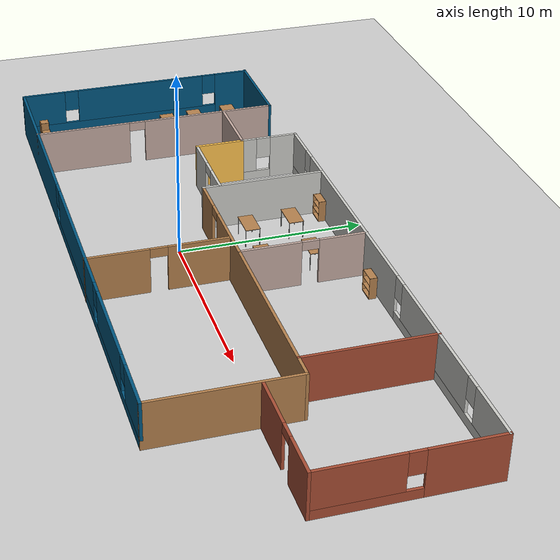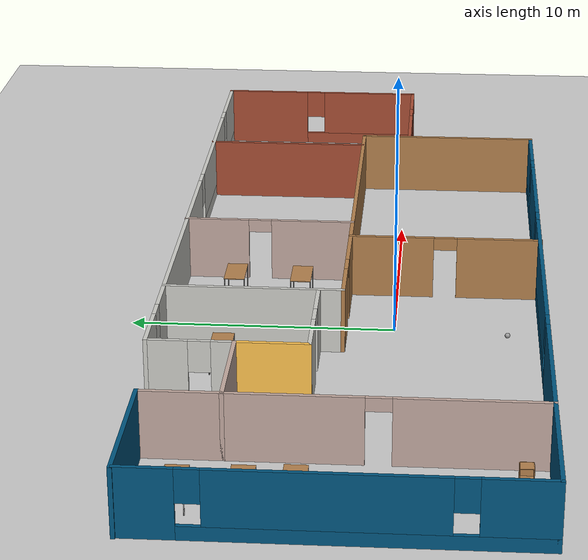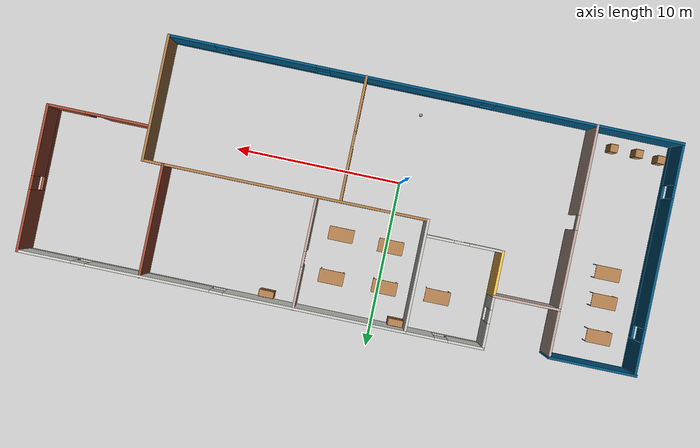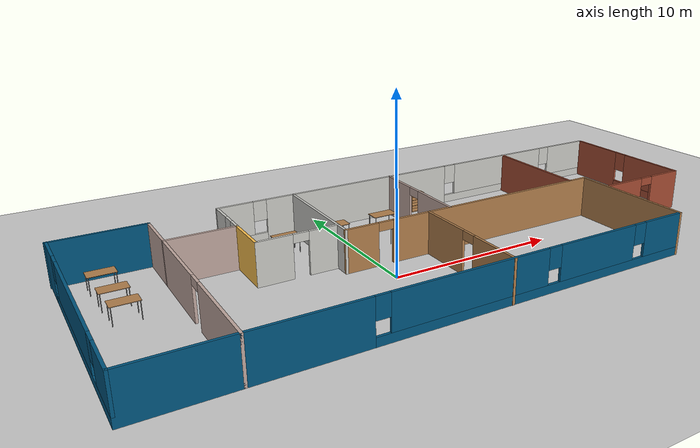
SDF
<sdf version="1.7">
 <world name="default">
  <light name="sun" type="directional">
   <pose>0 0 10 0 -0 0</pose>
   <diffuse>0.8 0.8 0.8 1</diffuse>
   <specular>0.2 0.2 0.2 1</specular>
   <attenuation>
    <range>1000</range>
    <constant>0.9</constant>
    <linear>0.01</linear>
    <quadratic>0.001</quadratic>
   </attenuation>
   <direction>-0.5 0.1 -0.9</direction>
   <spot><inner_angle>0</inner_angle><outer_angle>0</outer_angle><falloff>0</falloff></spot>
  </light>
  <model name="ground_plane">
   <static>1</static>
   <link name="link">
    <collision name="collision">
     <geometry><plane><normal>0 0 1</normal><size>100 100</size></plane></geometry>
     <surface>
      <contact><collide_bitmask>65535</collide_bitmask></contact>
      <friction><ode><mu>100</mu><mu2>50</mu2></ode></friction>
     </surface>
    </collision>
    <visual name="visual">
     <cast_shadows>0</cast_shadows>
     <geometry><plane><normal>0 0 1</normal><size>100 100</size></plane></geometry>
     <material>
      <script><uri>file://media/materials/scripts/gazebo.material</uri><name>Gazebo/Grey</name></script>
     </material>
    </visual>
   </link>
  </model>
  <gravity>0 0 -9.8</gravity>
  <magnetic_field>6e-06 2.3e-05 -4.2e-05</magnetic_field>
  <atmosphere type="adiabatic"/>
  <physics type="ode">
   <max_step_size>0.001</max_step_size>
   <real_time_factor>1</real_time_factor>
   <real_time_update_rate>1000</real_time_update_rate>
  </physics>
  <scene><ambient>0.4 0.4 0.4 1</ambient><background>0.7 0.7 0.7 1</background><shadows>1</shadows></scene>
  <spherical_coordinates>
   <surface_model>EARTH_WGS84</surface_model>
   <latitude_deg>0</latitude_deg>
   <longitude_deg>0</longitude_deg>
   <elevation>0</elevation>
   <heading_deg>0</heading_deg>
  </spherical_coordinates>
  <model name="sohini_building">
   <pose>2.69266 1.47265 0 0 -0 0</pose>
   <link name="Wall_10">
    <collision name="Wall_10_Collision">
     <geometry><box><size>4 0.15 2.5</size></box></geometry>
     <pose>0 0 1.25 0 -0 0</pose>
    </collision>
    <visual name="Wall_10_Visual">
     <pose>0 0 1.25 0 -0 0</pose>
     <geometry><box><size>4 0.15 2.5</size></box></geometry>
     <material>
      <script><uri>file://media/materials/scripts/gazebo.material</uri><name>Gazebo/Grey</name></script>
      <ambient>0.760784 0.662745 0.627451 1</ambient>
     </material>
     <meta><layer>0</layer></meta>
    </visual>
    <pose>-11.175 3.87696 0 0 -0 3.14159</pose>
   </link>
   <link name="Wall_11">
    <collision name="Wall_11_Collision">
     <geometry><box><size>2.93882 0.15 2.5</size></box></geometry>
     <pose>0 0 1.25 0 -0 0</pose>
    </collision>
    <visual name="Wall_11_Visual">
     <pose>0 0 1.25 0 -0 0</pose>
     <geometry><box><size>2.93882 0.15 2.5</size></box></geometry>
     <material>
      <script><uri>file://media/materials/scripts/gazebo.material</uri><name>Gazebo/Grey</name></script>
      <ambient>0.760784 0.662745 0.627451 1</ambient>
     </material>
     <meta><layer>0</layer></meta>
    </visual>
    <pose>-13.1 5.27137 0 0 -0 1.5708</pose>
   </link>
   <link name="Wall_12">
    <collision name="Wall_12_Collision">
     <geometry><box><size>5.25 0.15 2.5</size></box></geometry>
     <pose>0 0 1.25 0 -0 0</pose>
    </collision>
    <visual name="Wall_12_Visual">
     <pose>0 0 1.25 0 -0 0</pose>
     <geometry><box><size>5.25 0.15 2.5</size></box></geometry>
     <material>
      <script><uri>file://media/materials/scripts/gazebo.material</uri><name>Gazebo/Grey</name></script>
      <ambient>0 0.333333 0.498039 1</ambient>
     </material>
     <meta><layer>0</layer></meta>
    </visual>
    <pose>-15.65 6.69637 0 0 -0 3.14159</pose>
   </link>
   <link name="Wall_14">
    <pose>6.775 6.97696 0 0 -0 0</pose>
    <visual name="Wall_14_Visual_0">
     <pose>-6.08464 0 1.25 0 -0 0</pose>
     <geometry><box><size>10.8307 0.15 2.5</size></box></geometry>
     <material>
      <script><uri>file://media/materials/scripts/gazebo.material</uri><name>Gazebo/CeilingTiled</name></script>
      <ambient>0.435294 0.796078 0.67451 1</ambient>
     </material>
     <meta><layer>0</layer></meta>
    </visual>
    <collision name="Wall_14_Collision_0">
     <geometry><box><size>10.8307 0.15 2.5</size></box></geometry>
     <pose>-6.08464 0 1.25 0 -0 0</pose>
    </collision>
    <visual name="Wall_14_Visual_1">
     <pose>5.41536 0 0.25 0 -0 0</pose>
     <geometry><box><size>12.1693 0.15 0.5</size></box></geometry>
     <material>
      <script><uri>file://media/materials/scripts/gazebo.material</uri><name>Gazebo/CeilingTiled</name></script>
      <ambient>0.435294 0.796078 0.67451 1</ambient>
     </material>
     <meta><layer>0</layer></meta>
    </visual>
    <collision name="Wall_14_Collision_1">
     <geometry><box><size>12.1693 0.15 0.5</size></box></geometry>
     <pose>5.41536 0 0.25 0 -0 0</pose>
    </collision>
    <visual name="Wall_14_Visual_2">
     <pose>3.79922 0 1.5 0 -0 0</pose>
     <geometry><box><size>7.337 0.15 2</size></box></geometry>
     <material>
      <script><uri>file://media/materials/scripts/gazebo.material</uri><name>Gazebo/CeilingTiled</name></script>
      <ambient>0.435294 0.796078 0.67451 1</ambient>
     </material>
     <meta><layer>0</layer></meta>
    </visual>
    <collision name="Wall_14_Collision_2">
     <geometry><box><size>7.337 0.15 2</size></box></geometry>
     <pose>3.79922 0 1.5 0 -0 0</pose>
    </collision>
    <visual name="Wall_14_Visual_3">
     <pose>9.88386 0 1.5 0 -0 0</pose>
     <geometry><box><size>3.23228 0.15 2</size></box></geometry>
     <material>
      <script><uri>file://media/materials/scripts/gazebo.material</uri><name>Gazebo/CeilingTiled</name></script>
      <ambient>0.435294 0.796078 0.67451 1</ambient>
     </material>
     <meta><layer>0</layer></meta>
    </visual>
    <collision name="Wall_14_Collision_3">
     <geometry><box><size>3.23228 0.15 2</size></box></geometry>
     <pose>9.88386 0 1.5 0 -0 0</pose>
    </collision>
    <visual name="Wall_14_Visual_4">
     <pose>-0.269276 0 1.9 0 -0 0</pose>
     <geometry><box><size>0.8 0.15 1.2</size></box></geometry>
     <material>
      <script><uri>file://media/materials/scripts/gazebo.material</uri><name>Gazebo/CeilingTiled</name></script>
      <ambient>0.435294 0.796078 0.67451 1</ambient>
     </material>
     <meta><layer>0</layer></meta>
    </visual>
    <collision name="Wall_14_Collision_4">
     <geometry><box><size>0.8 0.15 1.2</size></box></geometry>
     <pose>-0.269276 0 1.9 0 -0 0</pose>
    </collision>
    <visual name="Wall_14_Visual_5">
     <pose>7.86772 0 1.9 0 -0 0</pose>
     <geometry><box><size>0.8 0.15 1.2</size></box></geometry>
     <material>
      <script><uri>file://media/materials/scripts/gazebo.material</uri><name>Gazebo/CeilingTiled</name></script>
      <ambient>0.435294 0.796078 0.67451 1</ambient>
     </material>
     <meta><layer>0</layer></meta>
    </visual>
    <collision name="Wall_14_Collision_5">
     <geometry><box><size>0.8 0.15 1.2</size></box></geometry>
     <pose>7.86772 0 1.9 0 -0 0</pose>
    </collision>
   </link>
   <link name="Wall_15">
    <pose>18.2 2.67696 0 0 -0 -1.5708</pose>
    <visual name="Wall_15_Visual_0">
     <pose>-2.52709 0 1.25 0 -0 0</pose>
     <geometry><box><size>3.69583 0.15 2.5</size></box></geometry>
     <material>
      <script><uri>file://media/materials/scripts/gazebo.material</uri><name>Gazebo/Bricks</name></script>
      <ambient>1 1 1 1</ambient>
     </material>
     <meta><layer>0</layer></meta>
    </visual>
    <collision name="Wall_15_Collision_0">
     <geometry><box><size>3.69583 0.15 2.5</size></box></geometry>
     <pose>-2.52709 0 1.25 0 -0 0</pose>
    </collision>
    <visual name="Wall_15_Visual_1">
     <pose>1.84791 0 0.25 0 -0 0</pose>
     <geometry><box><size>5.05417 0.15 0.5</size></box></geometry>
     <material>
      <script><uri>file://media/materials/scripts/gazebo.material</uri><name>Gazebo/Bricks</name></script>
      <ambient>1 1 1 1</ambient>
     </material>
     <meta><layer>0</layer></meta>
    </visual>
    <collision name="Wall_15_Collision_1">
     <geometry><box><size>5.05417 0.15 0.5</size></box></geometry>
     <pose>1.84791 0 0.25 0 -0 0</pose>
    </collision>
    <visual name="Wall_15_Visual_2">
     <pose>2.24791 0 1.5 0 -0 0</pose>
     <geometry><box><size>4.25417 0.15 2</size></box></geometry>
     <material>
      <script><uri>file://media/materials/scripts/gazebo.material</uri><name>Gazebo/Bricks</name></script>
      <ambient>1 1 1 1</ambient>
     </material>
     <meta><layer>0</layer></meta>
    </visual>
    <collision name="Wall_15_Collision_2">
     <geometry><box><size>4.25417 0.15 2</size></box></geometry>
     <pose>2.24791 0 1.5 0 -0 0</pose>
    </collision>
    <visual name="Wall_15_Visual_3">
     <pose>-0.279172 0 1.9 0 -0 0</pose>
     <geometry><box><size>0.8 0.15 1.2</size></box></geometry>
     <material>
      <script><uri>file://media/materials/scripts/gazebo.material</uri><name>Gazebo/Bricks</name></script>
      <ambient>1 1 1 1</ambient>
     </material>
     <meta><layer>0</layer></meta>
    </visual>
    <collision name="Wall_15_Collision_3">
     <geometry><box><size>0.8 0.15 1.2</size></box></geometry>
     <pose>-0.279172 0 1.9 0 -0 0</pose>
    </collision>
   </link>
   <link name="Wall_16">
    <pose>15.275 -1.62304 0 0 -0 3.14159</pose>
    <visual name="Wall_16_Visual_0">
     <pose>-1.85242 0 1.25 0 -0 0</pose>
     <geometry><box><size>2.29516 0.15 2.5</size></box></geometry>
     <material>
      <script><uri>file://media/materials/scripts/gazebo.material</uri><name>Gazebo/Bricks</name></script>
      <ambient>1 1 1 1</ambient>
     </material>
     <meta><layer>0</layer></meta>
    </visual>
    <collision name="Wall_16_Collision_0">
     <geometry><box><size>2.29516 0.15 2.5</size></box></geometry>
     <pose>-1.85242 0 1.25 0 -0 0</pose>
    </collision>
    <visual name="Wall_16_Visual_1">
     <pose>1.59758 0 1.25 0 -0 0</pose>
     <geometry><box><size>2.80484 0.15 2.5</size></box></geometry>
     <material>
      <script><uri>file://media/materials/scripts/gazebo.material</uri><name>Gazebo/Bricks</name></script>
      <ambient>1 1 1 1</ambient>
     </material>
     <meta><layer>0</layer></meta>
    </visual>
    <collision name="Wall_16_Collision_1">
     <geometry><box><size>2.80484 0.15 2.5</size></box></geometry>
     <pose>1.59758 0 1.25 0 -0 0</pose>
    </collision>
    <visual name="Wall_16_Visual_2">
     <pose>-0.254841 0 2.25 0 -0 0</pose>
     <geometry><box><size>0.9 0.15 0.5</size></box></geometry>
     <material>
      <script><uri>file://media/materials/scripts/gazebo.material</uri><name>Gazebo/Bricks</name></script>
      <ambient>1 1 1 1</ambient>
     </material>
     <meta><layer>0</layer></meta>
    </visual>
    <collision name="Wall_16_Collision_2">
     <geometry><box><size>0.9 0.15 0.5</size></box></geometry>
     <pose>-0.254841 0 2.25 0 -0 0</pose>
    </collision>
   </link>
   <link name="Wall_18">
    <pose>1.94778 3.69404 0 0 -0 -1.5708</pose>
    <visual name="Wall_18_Visual_0">
     <pose>-2.09417 0 1.25 0 -0 0</pose>
     <geometry><box><size>2.56166 0.15 2.5</size></box></geometry>
     <material>
      <script><uri>file://media/materials/scripts/gazebo.material</uri><name>Gazebo/Grey</name></script>
      <ambient>0.760784 0.662745 0.627451 1</ambient>
     </material>
     <meta><layer>0</layer></meta>
    </visual>
    <collision name="Wall_18_Collision_0">
     <geometry><box><size>2.56166 0.15 2.5</size></box></geometry>
     <pose>-2.09417 0 1.25 0 -0 0</pose>
    </collision>
    <visual name="Wall_18_Visual_1">
     <pose>1.73083 0 1.25 0 -0 0</pose>
     <geometry><box><size>3.28834 0.15 2.5</size></box></geometry>
     <material>
      <script><uri>file://media/materials/scripts/gazebo.material</uri><name>Gazebo/Grey</name></script>
      <ambient>0.760784 0.662745 0.627451 1</ambient>
     </material>
     <meta><layer>0</layer></meta>
    </visual>
    <collision name="Wall_18_Collision_1">
     <geometry><box><size>3.28834 0.15 2.5</size></box></geometry>
     <pose>1.73083 0 1.25 0 -0 0</pose>
    </collision>
    <visual name="Wall_18_Visual_2">
     <pose>-0.363338 0 2.25 0 -0 0</pose>
     <geometry><box><size>0.9 0.15 0.5</size></box></geometry>
     <material>
      <script><uri>file://media/materials/scripts/gazebo.material</uri><name>Gazebo/Grey</name></script>
      <ambient>0.760784 0.662745 0.627451 1</ambient>
     </material>
     <meta><layer>0</layer></meta>
    </visual>
    <collision name="Wall_18_Collision_2">
     <geometry><box><size>0.9 0.15 0.5</size></box></geometry>
     <pose>-0.363338 0 2.25 0 -0 0</pose>
    </collision>
   </link>
   <link name="Wall_20">
    <collision name="Wall_20_Collision">
     <geometry><box><size>6.75 0.15 2.5</size></box></geometry>
     <pose>0 0 1.25 0 -0 0</pose>
    </collision>
    <visual name="Wall_20_Visual">
     <pose>0 0 1.25 0 -0 0</pose>
     <geometry><box><size>6.75 0.15 2.5</size></box></geometry>
     <material>
      <script><uri>file://media/materials/scripts/gazebo.material</uri><name>Gazebo/Bricks</name></script>
      <ambient>1 1 1 1</ambient>
     </material>
     <meta><layer>0</layer></meta>
    </visual>
    <pose>11.0025 3.69404 0 0 -0 -1.5708</pose>
   </link>
   <link name="Wall_22">
    <pose>-13.1 -1.54804 0 0 -0 -1.5708</pose>
    <visual name="Wall_22_Visual_0">
     <pose>-3.11636 0 1.25 0 -0 0</pose>
     <geometry><box><size>4.76728 0.15 2.5</size></box></geometry>
     <material>
      <script><uri>file://media/materials/scripts/gazebo.material</uri><name>Gazebo/Grey</name></script>
      <ambient>0.760784 0.662745 0.627451 1</ambient>
     </material>
     <meta><layer>0</layer></meta>
    </visual>
    <collision name="Wall_22_Collision_0">
     <geometry><box><size>4.76728 0.15 2.5</size></box></geometry>
     <pose>-3.11636 0 1.25 0 -0 0</pose>
    </collision>
    <visual name="Wall_22_Visual_1">
     <pose>2.83364 0 1.25 0 -0 0</pose>
     <geometry><box><size>5.33272 0.15 2.5</size></box></geometry>
     <material>
      <script><uri>file://media/materials/scripts/gazebo.material</uri><name>Gazebo/Grey</name></script>
      <ambient>0.760784 0.662745 0.627451 1</ambient>
     </material>
     <meta><layer>0</layer></meta>
    </visual>
    <collision name="Wall_22_Collision_1">
     <geometry><box><size>5.33272 0.15 2.5</size></box></geometry>
     <pose>2.83364 0 1.25 0 -0 0</pose>
    </collision>
    <visual name="Wall_22_Visual_2">
     <pose>-0.282721 0 2.25 0 -0 0</pose>
     <geometry><box><size>0.9 0.15 0.5</size></box></geometry>
     <material>
      <script><uri>file://media/materials/scripts/gazebo.material</uri><name>Gazebo/Grey</name></script>
      <ambient>0.760784 0.662745 0.627451 1</ambient>
     </material>
     <meta><layer>0</layer></meta>
    </visual>
    <collision name="Wall_22_Collision_2">
     <geometry><box><size>0.9 0.15 0.5</size></box></geometry>
     <pose>-0.282721 0 2.25 0 -0 0</pose>
    </collision>
   </link>
   <link name="Wall_26">
    <collision name="Wall_26_Collision">
     <geometry><box><size>2.75 0.15 2.5</size></box></geometry>
     <pose>0 0 1.25 0 -0 0</pose>
    </collision>
    <visual name="Wall_26_Visual">
     <pose>0 0 1.25 0 -0 0</pose>
     <geometry><box><size>2.75 0.15 2.5</size></box></geometry>
     <material>
      <script><uri>file://media/materials/scripts/gazebo.material</uri><name>Gazebo/Grey</name></script>
      <ambient>1 0.764706 0.305882 1</ambient>
     </material>
     <meta><layer>0</layer></meta>
    </visual>
    <pose>-9.25 2.57696 0 0 -0 -1.5708</pose>
   </link>
   <link name="Wall_27">
    <pose>-6.95 1.27696 0 0 -0 0</pose>
    <visual name="Wall_27_Visual_0">
     <pose>-1.33801 0 1.25 0 -0 0</pose>
     <geometry><box><size>2.07397 0.15 2.5</size></box></geometry>
     <material>
      <script><uri>file://media/materials/scripts/gazebo.material</uri><name>Gazebo/CeilingTiled</name></script>
      <ambient>1 0.764706 0.305882 1</ambient>
     </material>
     <meta><layer>0</layer></meta>
    </visual>
    <collision name="Wall_27_Collision_0">
     <geometry><box><size>2.07397 0.15 2.5</size></box></geometry>
     <pose>-1.33801 0 1.25 0 -0 0</pose>
    </collision>
    <visual name="Wall_27_Visual_1">
     <pose>1.48699 0 1.25 0 -0 0</pose>
     <geometry><box><size>1.77602 0.15 2.5</size></box></geometry>
     <material>
      <script><uri>file://media/materials/scripts/gazebo.material</uri><name>Gazebo/CeilingTiled</name></script>
      <ambient>1 0.764706 0.305882 1</ambient>
     </material>
     <meta><layer>0</layer></meta>
    </visual>
    <collision name="Wall_27_Collision_1">
     <geometry><box><size>1.77602 0.15 2.5</size></box></geometry>
     <pose>1.48699 0 1.25 0 -0 0</pose>
    </collision>
    <visual name="Wall_27_Visual_2">
     <pose>0.148975 0 2.25 0 -0 0</pose>
     <geometry><box><size>0.9 0.15 0.5</size></box></geometry>
     <material>
      <script><uri>file://media/materials/scripts/gazebo.material</uri><name>Gazebo/CeilingTiled</name></script>
      <ambient>1 0.764706 0.305882 1</ambient>
     </material>
     <meta><layer>0</layer></meta>
    </visual>
    <collision name="Wall_27_Collision_2">
     <geometry><box><size>0.9 0.15 0.5</size></box></geometry>
     <pose>0.148975 0 2.25 0 -0 0</pose>
    </collision>
   </link>
   <link name="Wall_29">
    <pose>0.540629 -3.31904 0 0 -0 -1.5708</pose>
    <visual name="Wall_29_Visual_0">
     <pose>-2.10209 0 1.25 0 -0 0</pose>
     <geometry><box><size>3.29583 0.15 2.5</size></box></geometry>
     <material>
      <script><uri>file://media/materials/scripts/gazebo.material</uri><name>Gazebo/Wood</name></script>
      <ambient>1 1 1 1</ambient>
     </material>
     <meta><layer>0</layer></meta>
    </visual>
    <collision name="Wall_29_Collision_0">
     <geometry><box><size>3.29583 0.15 2.5</size></box></geometry>
     <pose>-2.10209 0 1.25 0 -0 0</pose>
    </collision>
    <visual name="Wall_29_Visual_1">
     <pose>2.09791 0 1.25 0 -0 0</pose>
     <geometry><box><size>3.30417 0.15 2.5</size></box></geometry>
     <material>
      <script><uri>file://media/materials/scripts/gazebo.material</uri><name>Gazebo/Wood</name></script>
      <ambient>1 1 1 1</ambient>
     </material>
     <meta><layer>0</layer></meta>
    </visual>
    <collision name="Wall_29_Collision_1">
     <geometry><box><size>3.30417 0.15 2.5</size></box></geometry>
     <pose>2.09791 0 1.25 0 -0 0</pose>
    </collision>
    <visual name="Wall_29_Visual_2">
     <pose>-0.004173 0 2.25 0 -0 0</pose>
     <geometry><box><size>0.9 0.15 0.5</size></box></geometry>
     <material>
      <script><uri>file://media/materials/scripts/gazebo.material</uri><name>Gazebo/Wood</name></script>
      <ambient>1 1 1 1</ambient>
     </material>
     <meta><layer>0</layer></meta>
    </visual>
    <collision name="Wall_29_Collision_2">
     <geometry><box><size>0.9 0.15 0.5</size></box></geometry>
     <pose>-0.004173 0 2.25 0 -0 0</pose>
    </collision>
   </link>
   <link name="Wall_3">
    <pose>-18.15 -0.173043 0 0 -0 -1.5708</pose>
    <visual name="Wall_3_Visual_0">
     <pose>-5.90566 0 1.25 0 -0 0</pose>
     <geometry><box><size>1.93868 0.15 2.5</size></box></geometry>
     <material>
      <script><uri>file://media/materials/scripts/gazebo.material</uri><name>Gazebo/Grey</name></script>
      <ambient>0 0.333333 0.498039 1</ambient>
     </material>
     <meta><layer>0</layer></meta>
    </visual>
    <collision name="Wall_3_Collision_0">
     <geometry><box><size>1.93868 0.15 2.5</size></box></geometry>
     <pose>-5.90566 0 1.25 0 -0 0</pose>
    </collision>
    <visual name="Wall_3_Visual_1">
     <pose>0.969339 0 0.25 0 -0 0</pose>
     <geometry><box><size>11.8113 0.15 0.5</size></box></geometry>
     <material>
      <script><uri>file://media/materials/scripts/gazebo.material</uri><name>Gazebo/Grey</name></script>
      <ambient>0 0.333333 0.498039 1</ambient>
     </material>
     <meta><layer>0</layer></meta>
    </visual>
    <collision name="Wall_3_Collision_1">
     <geometry><box><size>11.8113 0.15 0.5</size></box></geometry>
     <pose>0.969339 0 0.25 0 -0 0</pose>
    </collision>
    <visual name="Wall_3_Visual_2">
     <pose>-0.284281 0 1.5 0 -0 0</pose>
     <geometry><box><size>7.70408 0.15 2</size></box></geometry>
     <material>
      <script><uri>file://media/materials/scripts/gazebo.material</uri><name>Gazebo/Grey</name></script>
      <ambient>0 0.333333 0.498039 1</ambient>
     </material>
     <meta><layer>0</layer></meta>
    </visual>
    <collision name="Wall_3_Collision_2">
     <geometry><box><size>7.70408 0.15 2</size></box></geometry>
     <pose>-0.284281 0 1.5 0 -0 0</pose>
    </collision>
    <visual name="Wall_3_Visual_3">
     <pose>5.62138 0 1.5 0 -0 0</pose>
     <geometry><box><size>2.50724 0.15 2</size></box></geometry>
     <material>
      <script><uri>file://media/materials/scripts/gazebo.material</uri><name>Gazebo/Grey</name></script>
      <ambient>0 0.333333 0.498039 1</ambient>
     </material>
     <meta><layer>0</layer></meta>
    </visual>
    <collision name="Wall_3_Collision_3">
     <geometry><box><size>2.50724 0.15 2</size></box></geometry>
     <pose>5.62138 0 1.5 0 -0 0</pose>
    </collision>
    <visual name="Wall_3_Visual_4">
     <pose>-4.53632 0 1.9 0 -0 0</pose>
     <geometry><box><size>0.8 0.15 1.2</size></box></geometry>
     <material>
      <script><uri>file://media/materials/scripts/gazebo.material</uri><name>Gazebo/Grey</name></script>
      <ambient>0 0.333333 0.498039 1</ambient>
     </material>
     <meta><layer>0</layer></meta>
    </visual>
    <collision name="Wall_3_Collision_4">
     <geometry><box><size>0.8 0.15 1.2</size></box></geometry>
     <pose>-4.53632 0 1.9 0 -0 0</pose>
    </collision>
    <visual name="Wall_3_Visual_5">
     <pose>3.96776 0 1.9 0 -0 0</pose>
     <geometry><box><size>0.8 0.15 1.2</size></box></geometry>
     <material>
      <script><uri>file://media/materials/scripts/gazebo.material</uri><name>Gazebo/Grey</name></script>
      <ambient>0 0.333333 0.498039 1</ambient>
     </material>
     <meta><layer>0</layer></meta>
    </visual>
    <collision name="Wall_3_Collision_5">
     <geometry><box><size>0.8 0.15 1.2</size></box></geometry>
     <pose>3.96776 0 1.9 0 -0 0</pose>
    </collision>
   </link>
   <link name="Wall_4">
    <pose>-2.975 -6.97304 0 0 -0 0</pose>
    <visual name="Wall_4_Visual_0">
     <pose>-9.70742 0 1.25 0 -0 0</pose>
     <geometry><box><size>11.0852 0.15 2.5</size></box></geometry>
     <material>
      <script><uri>file://media/materials/scripts/gazebo.material</uri><name>Gazebo/Grey</name></script>
      <ambient>0 0.333333 0.498039 1</ambient>
     </material>
     <meta><layer>0</layer></meta>
    </visual>
    <collision name="Wall_4_Collision_0">
     <geometry><box><size>11.0852 0.15 2.5</size></box></geometry>
     <pose>-9.70742 0 1.25 0 -0 0</pose>
    </collision>
    <visual name="Wall_4_Visual_1">
     <pose>5.54258 0 0.25 0 -0 0</pose>
     <geometry><box><size>19.4148 0.15 0.5</size></box></geometry>
     <material>
      <script><uri>file://media/materials/scripts/gazebo.material</uri><name>Gazebo/Grey</name></script>
      <ambient>0 0.333333 0.498039 1</ambient>
     </material>
     <meta><layer>0</layer></meta>
    </visual>
    <collision name="Wall_4_Collision_1">
     <geometry><box><size>19.4148 0.15 0.5</size></box></geometry>
     <pose>5.54258 0 0.25 0 -0 0</pose>
    </collision>
    <visual name="Wall_4_Visual_2">
     <pose>1.16018 0 1.5 0 -0 0</pose>
     <geometry><box><size>9.05005 0.15 2</size></box></geometry>
     <material>
      <script><uri>file://media/materials/scripts/gazebo.material</uri><name>Gazebo/Grey</name></script>
      <ambient>0 0.333333 0.498039 1</ambient>
     </material>
     <meta><layer>0</layer></meta>
    </visual>
    <collision name="Wall_4_Collision_2">
     <geometry><box><size>9.05005 0.15 2</size></box></geometry>
     <pose>1.16018 0 1.5 0 -0 0</pose>
    </collision>
    <visual name="Wall_4_Visual_3">
     <pose>9.06776 0 1.5 0 -0 0</pose>
     <geometry><box><size>5.16509 0.15 2</size></box></geometry>
     <material>
      <script><uri>file://media/materials/scripts/gazebo.material</uri><name>Gazebo/Grey</name></script>
      <ambient>0 0.333333 0.498039 1</ambient>
     </material>
     <meta><layer>0</layer></meta>
    </visual>
    <collision name="Wall_4_Collision_3">
     <geometry><box><size>5.16509 0.15 2</size></box></geometry>
     <pose>9.06776 0 1.5 0 -0 0</pose>
    </collision>
    <visual name="Wall_4_Visual_4">
     <pose>13.8502 0 1.5 0 -0 0</pose>
     <geometry><box><size>2.7997 0.15 2</size></box></geometry>
     <material>
      <script><uri>file://media/materials/scripts/gazebo.material</uri><name>Gazebo/Grey</name></script>
      <ambient>0 0.333333 0.498039 1</ambient>
     </material>
     <meta><layer>0</layer></meta>
    </visual>
    <collision name="Wall_4_Collision_4">
     <geometry><box><size>2.7997 0.15 2</size></box></geometry>
     <pose>13.8502 0 1.5 0 -0 0</pose>
    </collision>
    <visual name="Wall_4_Visual_5">
     <pose>-3.76485 0 1.9 0 -0 0</pose>
     <geometry><box><size>0.8 0.15 1.2</size></box></geometry>
     <material>
      <script><uri>file://media/materials/scripts/gazebo.material</uri><name>Gazebo/Grey</name></script>
      <ambient>0 0.333333 0.498039 1</ambient>
     </material>
     <meta><layer>0</layer></meta>
    </visual>
    <collision name="Wall_4_Collision_5">
     <geometry><box><size>0.8 0.15 1.2</size></box></geometry>
     <pose>-3.76485 0 1.9 0 -0 0</pose>
    </collision>
    <visual name="Wall_4_Visual_6">
     <pose>6.08521 0 1.9 0 -0 0</pose>
     <geometry><box><size>0.8 0.15 1.2</size></box></geometry>
     <material>
      <script><uri>file://media/materials/scripts/gazebo.material</uri><name>Gazebo/Grey</name></script>
      <ambient>0 0.333333 0.498039 1</ambient>
     </material>
     <meta><layer>0</layer></meta>
    </visual>
    <collision name="Wall_4_Collision_6">
     <geometry><box><size>0.8 0.15 1.2</size></box></geometry>
     <pose>6.08521 0 1.9 0 -0 0</pose>
    </collision>
    <visual name="Wall_4_Visual_7">
     <pose>12.0503 0 1.9 0 -0 0</pose>
     <geometry><box><size>0.8 0.15 1.2</size></box></geometry>
     <material>
      <script><uri>file://media/materials/scripts/gazebo.material</uri><name>Gazebo/Grey</name></script>
      <ambient>0 0.333333 0.498039 1</ambient>
     </material>
     <meta><layer>0</layer></meta>
    </visual>
    <collision name="Wall_4_Collision_7">
     <geometry><box><size>0.8 0.15 1.2</size></box></geometry>
     <pose>12.0503 0 1.9 0 -0 0</pose>
    </collision>
   </link>
   <link name="Wall_5">
    <collision name="Wall_5_Collision">
     <geometry><box><size>7.5 0.15 2.5</size></box></geometry>
     <pose>0 0 1.25 0 -0 0</pose>
    </collision>
    <visual name="Wall_5_Visual">
     <pose>0 0 1.25 0 -0 0</pose>
     <geometry><box><size>7.5 0.15 2.5</size></box></geometry>
     <material>
      <script><uri>file://media/materials/scripts/gazebo.material</uri><name>Gazebo/Wood</name></script>
      <ambient>1 1 1 1</ambient>
     </material>
     <meta><layer>0</layer></meta>
    </visual>
    <pose>12.2 -3.29804 0 0 -0 1.5708</pose>
   </link>
   <link name="Wall_6">
    <pose>3.775 0.376957 0 0 -0 3.14159</pose>
    <visual name="Wall_6_Visual_0">
     <pose>-1.46596 0 1.25 0 -0 0</pose>
     <geometry><box><size>14.0681 0.15 2.5</size></box></geometry>
     <material>
      <script><uri>file://media/materials/scripts/gazebo.material</uri><name>Gazebo/Wood</name></script>
      <ambient>1 1 1 1</ambient>
     </material>
     <meta><layer>0</layer></meta>
    </visual>
    <collision name="Wall_6_Collision_0">
     <geometry><box><size>14.0681 0.15 2.5</size></box></geometry>
     <pose>-1.46596 0 1.25 0 -0 0</pose>
    </collision>
    <visual name="Wall_6_Visual_1">
     <pose>7.48404 0 1.25 0 -0 0</pose>
     <geometry><box><size>2.03192 0.15 2.5</size></box></geometry>
     <material>
      <script><uri>file://media/materials/scripts/gazebo.material</uri><name>Gazebo/Wood</name></script>
      <ambient>1 1 1 1</ambient>
     </material>
     <meta><layer>0</layer></meta>
    </visual>
    <collision name="Wall_6_Collision_1">
     <geometry><box><size>2.03192 0.15 2.5</size></box></geometry>
     <pose>7.48404 0 1.25 0 -0 0</pose>
    </collision>
    <visual name="Wall_6_Visual_2">
     <pose>6.01808 0 2.25 0 -0 0</pose>
     <geometry><box><size>0.9 0.15 0.5</size></box></geometry>
     <material>
      <script><uri>file://media/materials/scripts/gazebo.material</uri><name>Gazebo/Wood</name></script>
      <ambient>1 1 1 1</ambient>
     </material>
     <meta><layer>0</layer></meta>
    </visual>
    <collision name="Wall_6_Collision_2">
     <geometry><box><size>0.9 0.15 0.5</size></box></geometry>
     <pose>6.01808 0 2.25 0 -0 0</pose>
    </collision>
   </link>
   <link name="Wall_7">
    <collision name="Wall_7_Collision">
     <geometry><box><size>6.75 0.15 2.5</size></box></geometry>
     <pose>0 0 1.25 0 -0 0</pose>
    </collision>
    <visual name="Wall_7_Visual">
     <pose>0 0 1.25 0 -0 0</pose>
     <geometry><box><size>6.75 0.15 2.5</size></box></geometry>
     <material>
      <script><uri>file://media/materials/scripts/gazebo.material</uri><name>Gazebo/CeilingTiled</name></script>
      <ambient>1 0.764706 0.305882 1</ambient>
     </material>
     <meta><layer>0</layer></meta>
    </visual>
    <pose>-4.65 3.67696 0 0 -0 1.5708</pose>
   </link>
   <link name="Wall_8">
    <pose>-6.95 6.97696 0 0 -0 3.14159</pose>
    <visual name="Wall_8_Visual_0">
     <pose>-1.47728 0 1.25 0 -0 0</pose>
     <geometry><box><size>1.79543 0.15 2.5</size></box></geometry>
     <material>
      <script><uri>file://media/materials/scripts/gazebo.material</uri><name>Gazebo/CeilingTiled</name></script>
      <ambient>1 0.764706 0.305882 1</ambient>
     </material>
     <meta><layer>0</layer></meta>
    </visual>
    <collision name="Wall_8_Collision_0">
     <geometry><box><size>1.79543 0.15 2.5</size></box></geometry>
     <pose>-1.47728 0 1.25 0 -0 0</pose>
    </collision>
    <visual name="Wall_8_Visual_1">
     <pose>0.897718 0 0.25 0 -0 0</pose>
     <geometry><box><size>2.95457 0.15 0.5</size></box></geometry>
     <material>
      <script><uri>file://media/materials/scripts/gazebo.material</uri><name>Gazebo/CeilingTiled</name></script>
      <ambient>1 0.764706 0.305882 1</ambient>
     </material>
     <meta><layer>0</layer></meta>
    </visual>
    <collision name="Wall_8_Collision_1">
     <geometry><box><size>2.95457 0.15 0.5</size></box></geometry>
     <pose>0.897718 0 0.25 0 -0 0</pose>
    </collision>
    <visual name="Wall_8_Visual_2">
     <pose>1.29772 0 1.5 0 -0 0</pose>
     <geometry><box><size>2.15456 0.15 2</size></box></geometry>
     <material>
      <script><uri>file://media/materials/scripts/gazebo.material</uri><name>Gazebo/CeilingTiled</name></script>
      <ambient>1 0.764706 0.305882 1</ambient>
     </material>
     <meta><layer>0</layer></meta>
    </visual>
    <collision name="Wall_8_Collision_2">
     <geometry><box><size>2.15456 0.15 2</size></box></geometry>
     <pose>1.29772 0 1.5 0 -0 0</pose>
    </collision>
    <visual name="Wall_8_Visual_3">
     <pose>-0.179565 0 1.9 0 -0 0</pose>
     <geometry><box><size>0.8 0.15 1.2</size></box></geometry>
     <material>
      <script><uri>file://media/materials/scripts/gazebo.material</uri><name>Gazebo/CeilingTiled</name></script>
      <ambient>1 0.764706 0.305882 1</ambient>
     </material>
     <meta><layer>0</layer></meta>
    </visual>
    <collision name="Wall_8_Collision_3">
     <geometry><box><size>0.8 0.15 1.2</size></box></geometry>
     <pose>-0.179565 0 1.9 0 -0 0</pose>
    </collision>
   </link>
   <link name="Wall_9">
    <pose>-9.25 5.42696 0 0 -0 -1.5708</pose>
    <visual name="Wall_9_Visual_0">
     <pose>-0.847744 0 1.25 0 -0 0</pose>
     <geometry><box><size>1.55451 0.15 2.5</size></box></geometry>
     <material>
      <script><uri>file://media/materials/scripts/gazebo.material</uri><name>Gazebo/CeilingTiled</name></script>
      <ambient>1 0.764706 0.305882 1</ambient>
     </material>
     <meta><layer>0</layer></meta>
    </visual>
    <collision name="Wall_9_Collision_0">
     <geometry><box><size>1.55451 0.15 2.5</size></box></geometry>
     <pose>-0.847744 0 1.25 0 -0 0</pose>
    </collision>
    <visual name="Wall_9_Visual_1">
     <pose>0.777256 0 0.25 0 -0 0</pose>
     <geometry><box><size>1.69549 0.15 0.5</size></box></geometry>
     <material>
      <script><uri>file://media/materials/scripts/gazebo.material</uri><name>Gazebo/CeilingTiled</name></script>
      <ambient>1 0.764706 0.305882 1</ambient>
     </material>
     <meta><layer>0</layer></meta>
    </visual>
    <collision name="Wall_9_Collision_1">
     <geometry><box><size>1.69549 0.15 0.5</size></box></geometry>
     <pose>0.777256 0 0.25 0 -0 0</pose>
    </collision>
    <visual name="Wall_9_Visual_2">
     <pose>1.17726 0 1.5 0 -0 0</pose>
     <geometry><box><size>0.895488 0.15 2</size></box></geometry>
     <material>
      <script><uri>file://media/materials/scripts/gazebo.material</uri><name>Gazebo/CeilingTiled</name></script>
      <ambient>1 0.764706 0.305882 1</ambient>
     </material>
     <meta><layer>0</layer></meta>
    </visual>
    <collision name="Wall_9_Collision_2">
     <geometry><box><size>0.895488 0.15 2</size></box></geometry>
     <pose>1.17726 0 1.5 0 -0 0</pose>
    </collision>
    <visual name="Wall_9_Visual_3">
     <pose>0.329512 0 1.9 0 -0 0</pose>
     <geometry><box><size>0.8 0.15 1.2</size></box></geometry>
     <material>
      <script><uri>file://media/materials/scripts/gazebo.material</uri><name>Gazebo/CeilingTiled</name></script>
      <ambient>1 0.764706 0.305882 1</ambient>
     </material>
     <meta><layer>0</layer></meta>
    </visual>
    <collision name="Wall_9_Collision_3">
     <geometry><box><size>0.8 0.15 1.2</size></box></geometry>
     <pose>0.329512 0 1.9 0 -0 0</pose>
    </collision>
   </link>
   <static>1</static>
  </model>
  <model name="ball">
   <link name="link_0">
    <inertial>
     <mass>1</mass>
     <inertia><ixx>0.1</ixx><ixy>0</ixy><ixz>0</ixz><iyy>0.1</iyy><iyz>0</iyz><izz>0.1</izz></inertia>
    </inertial>
    <visual name="visual">
     <geometry><sphere><radius>0.1</radius></sphere></geometry>
     <material>
      <lighting>1</lighting>
      <script><uri>file://media/materials/scripts/gazebo.material</uri><name>Gazebo/Grey</name></script>
      <shader type="pixel"><normal_map>__default__</normal_map></shader>
      <ambient>1 1 1 1</ambient>
      <diffuse>1 1 1 1</diffuse>
      <specular>1 1 1 1</specular>
      <emissive>1 1 1 1</emissive>
     </material>
    </visual>
    <collision name="collision">
     <geometry><sphere><radius>0.1</radius></sphere></geometry>
     <surface>
      <friction>
       <ode><mu>1</mu><mu2>1</mu2><fdir1>0 0 0</fdir1><slip1>0</slip1><slip2>0</slip2></ode>
       <torsional>
        <coefficient>1</coefficient>
        <patch_radius>0</patch_radius>
        <surface_radius>0</surface_radius>
        <use_patch_radius>1</use_patch_radius>
        <ode><slip>0</slip></ode>
       </torsional>
      </friction>
      <bounce><restitution_coefficient>0</restitution_coefficient><threshold>1e+06</threshold></bounce>
      <contact>
       <collide_without_contact>0</collide_without_contact>
       <collide_without_contact_bitmask>1</collide_without_contact_bitmask>
       <collide_bitmask>1</collide_bitmask>
       <ode>
        <soft_cfm>0</soft_cfm>
        <soft_erp>0.2</soft_erp>
        <kp>1e+13</kp>
        <kd>1</kd>
        <max_vel>0.01</max_vel>
        <min_depth>0</min_depth>
       </ode>
       <bullet>
        <split_impulse>1</split_impulse>
        <split_impulse_penetration_threshold>-0.01</split_impulse_penetration_threshold>
        <soft_cfm>0</soft_cfm>
        <soft_erp>0.2</soft_erp>
        <kp>1e+13</kp>
        <kd>1</kd>
       </bullet>
      </contact>
     </surface>
    </collision>
   </link>
   <static>0</static>
   <pose>-0.40279 -4.2561 0.1 0 -0 0</pose>
  </model>
  <model name="bookshelf">
   <static>1</static>
   <link name="link">
    <inertial><mass>1</mass></inertial>
    <collision name="back">
     <pose>0 0.005 0.6 0 -0 0</pose>
     <geometry><box><size>0.9 0.01 1.2</size></box></geometry>
    </collision>
    <visual name="visual1">
     <pose>0 0.005 0.6 0 -0 0</pose>
     <geometry><box><size>0.9 0.01 1.2</size></box></geometry>
     <material>
      <script><uri>file://media/materials/scripts/gazebo.material</uri><name>Gazebo/Wood</name></script>
     </material>
    </visual>
    <collision name="left_side">
     <pose>0.45 -0.195 0.6 0 -0 0</pose>
     <geometry><box><size>0.02 0.4 1.2</size></box></geometry>
    </collision>
    <visual name="visual2">
     <pose>0.45 -0.195 0.6 0 -0 0</pose>
     <geometry><box><size>0.02 0.4 1.2</size></box></geometry>
     <material>
      <script><uri>file://media/materials/scripts/gazebo.material</uri><name>Gazebo/Wood</name></script>
     </material>
    </visual>
    <collision name="right_side">
     <pose>-0.45 -0.195 0.6 0 -0 0</pose>
     <geometry><box><size>0.02 0.4 1.2</size></box></geometry>
    </collision>
    <visual name="visual3">
     <pose>-0.45 -0.195 0.6 0 -0 0</pose>
     <geometry><box><size>0.02 0.4 1.2</size></box></geometry>
     <material>
      <script><uri>file://media/materials/scripts/gazebo.material</uri><name>Gazebo/Wood</name></script>
     </material>
    </visual>
    <collision name="bottom">
     <pose>0 -0.195 0.03 0 -0 0</pose>
     <geometry><box><size>0.88 0.4 0.06</size></box></geometry>
    </collision>
    <visual name="visual4">
     <pose>0 -0.195 0.03 0 -0 0</pose>
     <geometry><box><size>0.88 0.4 0.06</size></box></geometry>
     <material>
      <script><uri>file://media/materials/scripts/gazebo.material</uri><name>Gazebo/Wood</name></script>
     </material>
    </visual>
    <collision name="top">
     <pose>0 -0.195 1.19 0 -0 0</pose>
     <geometry><box><size>0.88 0.4 0.02</size></box></geometry>
    </collision>
    <visual name="visual5">
     <pose>0 -0.195 1.19 0 -0 0</pose>
     <geometry><box><size>0.88 0.4 0.02</size></box></geometry>
     <material>
      <script><uri>file://media/materials/scripts/gazebo.material</uri><name>Gazebo/Wood</name></script>
     </material>
    </visual>
    <collision name="low_shelf">
     <pose>0 -0.195 0.43 0 -0 0</pose>
     <geometry><box><size>0.88 0.4 0.02</size></box></geometry>
    </collision>
    <visual name="visual6">
     <pose>0 -0.195 0.43 0 -0 0</pose>
     <geometry><box><size>0.88 0.4 0.02</size></box></geometry>
     <material>
      <script><uri>file://media/materials/scripts/gazebo.material</uri><name>Gazebo/Wood</name></script>
     </material>
    </visual>
    <collision name="high_shelf">
     <pose>0 -0.195 0.8 0 -0 0</pose>
     <geometry><box><size>0.88 0.4 0.02</size></box></geometry>
    </collision>
    <visual name="visual7">
     <pose>0 -0.195 0.8 0 -0 0</pose>
     <geometry><box><size>0.88 0.4 0.02</size></box></geometry>
     <material>
      <script><uri>file://media/materials/scripts/gazebo.material</uri><name>Gazebo/Wood</name></script>
     </material>
    </visual>
   </link>
   <pose>-1.39473 8.36492 0 0 -0 0</pose>
  </model>
  <model name="bookshelf_0">
   <static>1</static>
   <link name="link">
    <inertial><mass>1</mass></inertial>
    <collision name="back">
     <pose>0 0.005 0.6 0 -0 0</pose>
     <geometry><box><size>0.9 0.01 1.2</size></box></geometry>
    </collision>
    <visual name="visual1">
     <pose>0 0.005 0.6 0 -0 0</pose>
     <geometry><box><size>0.9 0.01 1.2</size></box></geometry>
     <material>
      <script><uri>file://media/materials/scripts/gazebo.material</uri><name>Gazebo/Wood</name></script>
     </material>
    </visual>
    <collision name="left_side">
     <pose>0.45 -0.195 0.6 0 -0 0</pose>
     <geometry><box><size>0.02 0.4 1.2</size></box></geometry>
    </collision>
    <visual name="visual2">
     <pose>0.45 -0.195 0.6 0 -0 0</pose>
     <geometry><box><size>0.02 0.4 1.2</size></box></geometry>
     <material>
      <script><uri>file://media/materials/scripts/gazebo.material</uri><name>Gazebo/Wood</name></script>
     </material>
    </visual>
    <collision name="right_side">
     <pose>-0.45 -0.195 0.6 0 -0 0</pose>
     <geometry><box><size>0.02 0.4 1.2</size></box></geometry>
    </collision>
    <visual name="visual3">
     <pose>-0.45 -0.195 0.6 0 -0 0</pose>
     <geometry><box><size>0.02 0.4 1.2</size></box></geometry>
     <material>
      <script><uri>file://media/materials/scripts/gazebo.material</uri><name>Gazebo/Wood</name></script>
     </material>
    </visual>
    <collision name="bottom">
     <pose>0 -0.195 0.03 0 -0 0</pose>
     <geometry><box><size>0.88 0.4 0.06</size></box></geometry>
    </collision>
    <visual name="visual4">
     <pose>0 -0.195 0.03 0 -0 0</pose>
     <geometry><box><size>0.88 0.4 0.06</size></box></geometry>
     <material>
      <script><uri>file://media/materials/scripts/gazebo.material</uri><name>Gazebo/Wood</name></script>
     </material>
    </visual>
    <collision name="top">
     <pose>0 -0.195 1.19 0 -0 0</pose>
     <geometry><box><size>0.88 0.4 0.02</size></box></geometry>
    </collision>
    <visual name="visual5">
     <pose>0 -0.195 1.19 0 -0 0</pose>
     <geometry><box><size>0.88 0.4 0.02</size></box></geometry>
     <material>
      <script><uri>file://media/materials/scripts/gazebo.material</uri><name>Gazebo/Wood</name></script>
     </material>
    </visual>
    <collision name="low_shelf">
     <pose>0 -0.195 0.43 0 -0 0</pose>
     <geometry><box><size>0.88 0.4 0.02</size></box></geometry>
    </collision>
    <visual name="visual6">
     <pose>0 -0.195 0.43 0 -0 0</pose>
     <geometry><box><size>0.88 0.4 0.02</size></box></geometry>
     <material>
      <script><uri>file://media/materials/scripts/gazebo.material</uri><name>Gazebo/Wood</name></script>
     </material>
    </visual>
    <collision name="high_shelf">
     <pose>0 -0.195 0.8 0 -0 0</pose>
     <geometry><box><size>0.88 0.4 0.02</size></box></geometry>
    </collision>
    <visual name="visual7">
     <pose>0 -0.195 0.8 0 -0 0</pose>
     <geometry><box><size>0.88 0.4 0.02</size></box></geometry>
     <material>
      <script><uri>file://media/materials/scripts/gazebo.material</uri><name>Gazebo/Wood</name></script>
     </material>
    </visual>
   </link>
   <pose>6.40986 8.26689 0 0 -0 0</pose>
  </model>
  <model name="table">
   <static>1</static>
   <link name="link">
    <collision name="surface">
     <pose>0 0 1 0 -0 0</pose>
     <geometry><box><size>1.5 0.8 0.03</size></box></geometry>
     <surface><friction><ode><mu>0.6</mu><mu2>0.6</mu2></ode></friction></surface>
    </collision>
    <visual name="visual1">
     <pose>0 0 1 0 -0 0</pose>
     <geometry><box><size>1.5 0.8 0.03</size></box></geometry>
     <material>
      <script><uri>file://media/materials/scripts/gazebo.material</uri><name>Gazebo/Wood</name></script>
     </material>
    </visual>
    <collision name="front_left_leg">
     <pose>0.68 0.38 0.5 0 -0 0</pose>
     <geometry><cylinder><radius>0.02</radius><length>1</length></cylinder></geometry>
    </collision>
    <visual name="front_left_leg">
     <pose>0.68 0.38 0.5 0 -0 0</pose>
     <geometry><cylinder><radius>0.02</radius><length>1</length></cylinder></geometry>
     <material>
      <script><uri>file://media/materials/scripts/gazebo.material</uri><name>Gazebo/Grey</name></script>
     </material>
    </visual>
    <collision name="front_right_leg">
     <pose>0.68 -0.38 0.5 0 -0 0</pose>
     <geometry><cylinder><radius>0.02</radius><length>1</length></cylinder></geometry>
    </collision>
    <visual name="front_right_leg">
     <pose>0.68 -0.38 0.5 0 -0 0</pose>
     <geometry><cylinder><radius>0.02</radius><length>1</length></cylinder></geometry>
     <material>
      <script><uri>file://media/materials/scripts/gazebo.material</uri><name>Gazebo/Grey</name></script>
     </material>
    </visual>
    <collision name="back_right_leg">
     <pose>-0.68 -0.38 0.5 0 -0 0</pose>
     <geometry><cylinder><radius>0.02</radius><length>1</length></cylinder></geometry>
    </collision>
    <visual name="back_right_leg">
     <pose>-0.68 -0.38 0.5 0 -0 0</pose>
     <geometry><cylinder><radius>0.02</radius><length>1</length></cylinder></geometry>
     <material>
      <script><uri>file://media/materials/scripts/gazebo.material</uri><name>Gazebo/Grey</name></script>
     </material>
    </visual>
    <collision name="back_left_leg">
     <pose>-0.68 0.38 0.5 0 -0 0</pose>
     <geometry><cylinder><radius>0.02</radius><length>1</length></cylinder></geometry>
    </collision>
    <visual name="back_left_leg">
     <pose>-0.68 0.38 0.5 0 -0 0</pose>
     <geometry><cylinder><radius>0.02</radius><length>1</length></cylinder></geometry>
     <material>
      <script><uri>file://media/materials/scripts/gazebo.material</uri><name>Gazebo/Grey</name></script>
     </material>
    </visual>
   </link>
   <pose>-13.3637 6.5418 0 0 -0 0</pose>
  </model>
  <model name="table_0">
   <static>1</static>
   <link name="link">
    <collision name="surface">
     <pose>0 0 1 0 -0 0</pose>
     <geometry><box><size>1.5 0.8 0.03</size></box></geometry>
     <surface><friction><ode><mu>0.6</mu><mu2>0.6</mu2></ode></friction></surface>
    </collision>
    <visual name="visual1">
     <pose>0 0 1 0 -0 0</pose>
     <geometry><box><size>1.5 0.8 0.03</size></box></geometry>
     <material>
      <script><uri>file://media/materials/scripts/gazebo.material</uri><name>Gazebo/Wood</name></script>
     </material>
    </visual>
    <collision name="front_left_leg">
     <pose>0.68 0.38 0.5 0 -0 0</pose>
     <geometry><cylinder><radius>0.02</radius><length>1</length></cylinder></geometry>
    </collision>
    <visual name="front_left_leg">
     <pose>0.68 0.38 0.5 0 -0 0</pose>
     <geometry><cylinder><radius>0.02</radius><length>1</length></cylinder></geometry>
     <material>
      <script><uri>file://media/materials/scripts/gazebo.material</uri><name>Gazebo/Grey</name></script>
     </material>
    </visual>
    <collision name="front_right_leg">
     <pose>0.68 -0.38 0.5 0 -0 0</pose>
     <geometry><cylinder><radius>0.02</radius><length>1</length></cylinder></geometry>
    </collision>
    <visual name="front_right_leg">
     <pose>0.68 -0.38 0.5 0 -0 0</pose>
     <geometry><cylinder><radius>0.02</radius><length>1</length></cylinder></geometry>
     <material>
      <script><uri>file://media/materials/scripts/gazebo.material</uri><name>Gazebo/Grey</name></script>
     </material>
    </visual>
    <collision name="back_right_leg">
     <pose>-0.68 -0.38 0.5 0 -0 0</pose>
     <geometry><cylinder><radius>0.02</radius><length>1</length></cylinder></geometry>
    </collision>
    <visual name="back_right_leg">
     <pose>-0.68 -0.38 0.5 0 -0 0</pose>
     <geometry><cylinder><radius>0.02</radius><length>1</length></cylinder></geometry>
     <material>
      <script><uri>file://media/materials/scripts/gazebo.material</uri><name>Gazebo/Grey</name></script>
     </material>
    </visual>
    <collision name="back_left_leg">
     <pose>-0.68 0.38 0.5 0 -0 0</pose>
     <geometry><cylinder><radius>0.02</radius><length>1</length></cylinder></geometry>
    </collision>
    <visual name="back_left_leg">
     <pose>-0.68 0.38 0.5 0 -0 0</pose>
     <geometry><cylinder><radius>0.02</radius><length>1</length></cylinder></geometry>
     <material>
      <script><uri>file://media/materials/scripts/gazebo.material</uri><name>Gazebo/Grey</name></script>
     </material>
    </visual>
   </link>
   <pose>-13.2475 4.41962 0 0 -0 0</pose>
  </model>
  <model name="table_1">
   <static>1</static>
   <link name="link">
    <collision name="surface">
     <pose>0 0 1 0 -0 0</pose>
     <geometry><box><size>1.5 0.8 0.03</size></box></geometry>
     <surface><friction><ode><mu>0.6</mu><mu2>0.6</mu2></ode></friction></surface>
    </collision>
    <visual name="visual1">
     <pose>0 0 1 0 -0 0</pose>
     <geometry><box><size>1.5 0.8 0.03</size></box></geometry>
     <material>
      <script><uri>file://media/materials/scripts/gazebo.material</uri><name>Gazebo/Wood</name></script>
     </material>
    </visual>
    <collision name="front_left_leg">
     <pose>0.68 0.38 0.5 0 -0 0</pose>
     <geometry><cylinder><radius>0.02</radius><length>1</length></cylinder></geometry>
    </collision>
    <visual name="front_left_leg">
     <pose>0.68 0.38 0.5 0 -0 0</pose>
     <geometry><cylinder><radius>0.02</radius><length>1</length></cylinder></geometry>
     <material>
      <script><uri>file://media/materials/scripts/gazebo.material</uri><name>Gazebo/Grey</name></script>
     </material>
    </visual>
    <collision name="front_right_leg">
     <pose>0.68 -0.38 0.5 0 -0 0</pose>
     <geometry><cylinder><radius>0.02</radius><length>1</length></cylinder></geometry>
    </collision>
    <visual name="front_right_leg">
     <pose>0.68 -0.38 0.5 0 -0 0</pose>
     <geometry><cylinder><radius>0.02</radius><length>1</length></cylinder></geometry>
     <material>
      <script><uri>file://media/materials/scripts/gazebo.material</uri><name>Gazebo/Grey</name></script>
     </material>
    </visual>
    <collision name="back_right_leg">
     <pose>-0.68 -0.38 0.5 0 -0 0</pose>
     <geometry><cylinder><radius>0.02</radius><length>1</length></cylinder></geometry>
    </collision>
    <visual name="back_right_leg">
     <pose>-0.68 -0.38 0.5 0 -0 0</pose>
     <geometry><cylinder><radius>0.02</radius><length>1</length></cylinder></geometry>
     <material>
      <script><uri>file://media/materials/scripts/gazebo.material</uri><name>Gazebo/Grey</name></script>
     </material>
    </visual>
    <collision name="back_left_leg">
     <pose>-0.68 0.38 0.5 0 -0 0</pose>
     <geometry><cylinder><radius>0.02</radius><length>1</length></cylinder></geometry>
    </collision>
    <visual name="back_left_leg">
     <pose>-0.68 0.38 0.5 0 -0 0</pose>
     <geometry><cylinder><radius>0.02</radius><length>1</length></cylinder></geometry>
     <material>
      <script><uri>file://media/materials/scripts/gazebo.material</uri><name>Gazebo/Grey</name></script>
     </material>
    </visual>
   </link>
   <pose>-13.1222 2.74764 0 0 -0 0</pose>
  </model>
  <model name="table_2">
   <static>1</static>
   <link name="link">
    <collision name="surface">
     <pose>0 0 1 0 -0 0</pose>
     <geometry><box><size>1.5 0.8 0.03</size></box></geometry>
     <surface><friction><ode><mu>0.6</mu><mu2>0.6</mu2></ode></friction></surface>
    </collision>
    <visual name="visual1">
     <pose>0 0 1 0 -0 0</pose>
     <geometry><box><size>1.5 0.8 0.03</size></box></geometry>
     <material>
      <script><uri>file://media/materials/scripts/gazebo.material</uri><name>Gazebo/Wood</name></script>
     </material>
    </visual>
    <collision name="front_left_leg">
     <pose>0.68 0.38 0.5 0 -0 0</pose>
     <geometry><cylinder><radius>0.02</radius><length>1</length></cylinder></geometry>
    </collision>
    <visual name="front_left_leg">
     <pose>0.68 0.38 0.5 0 -0 0</pose>
     <geometry><cylinder><radius>0.02</radius><length>1</length></cylinder></geometry>
     <material>
      <script><uri>file://media/materials/scripts/gazebo.material</uri><name>Gazebo/Grey</name></script>
     </material>
    </visual>
    <collision name="front_right_leg">
     <pose>0.68 -0.38 0.5 0 -0 0</pose>
     <geometry><cylinder><radius>0.02</radius><length>1</length></cylinder></geometry>
    </collision>
    <visual name="front_right_leg">
     <pose>0.68 -0.38 0.5 0 -0 0</pose>
     <geometry><cylinder><radius>0.02</radius><length>1</length></cylinder></geometry>
     <material>
      <script><uri>file://media/materials/scripts/gazebo.material</uri><name>Gazebo/Grey</name></script>
     </material>
    </visual>
    <collision name="back_right_leg">
     <pose>-0.68 -0.38 0.5 0 -0 0</pose>
     <geometry><cylinder><radius>0.02</radius><length>1</length></cylinder></geometry>
    </collision>
    <visual name="back_right_leg">
     <pose>-0.68 -0.38 0.5 0 -0 0</pose>
     <geometry><cylinder><radius>0.02</radius><length>1</length></cylinder></geometry>
     <material>
      <script><uri>file://media/materials/scripts/gazebo.material</uri><name>Gazebo/Grey</name></script>
     </material>
    </visual>
    <collision name="back_left_leg">
     <pose>-0.68 0.38 0.5 0 -0 0</pose>
     <geometry><cylinder><radius>0.02</radius><length>1</length></cylinder></geometry>
    </collision>
    <visual name="back_left_leg">
     <pose>-0.68 0.38 0.5 0 -0 0</pose>
     <geometry><cylinder><radius>0.02</radius><length>1</length></cylinder></geometry>
     <material>
      <script><uri>file://media/materials/scripts/gazebo.material</uri><name>Gazebo/Grey</name></script>
     </material>
    </visual>
   </link>
   <pose>-3.52259 6.17207 0 0 -0 0</pose>
  </model>
  <model name="cabinet">
   <static>1</static>
   <link name="cabinet_bottom_plate">
    <inertial>
     <pose>0 0 -1 0 -0 0</pose>
     <inertia><ixx>2.05</ixx><ixy>0</ixy><ixz>0</ixz><iyy>2.05</iyy><iyz>0</iyz><izz>2.05</izz></inertia>
     <mass>25</mass>
    </inertial>
    <collision name="cabinet_bottom_plate_geom">
     <pose>0 0 0.01 0 -0 0</pose>
     <geometry><box><size>0.45 0.45 0.02</size></box></geometry>
    </collision>
    <visual name="cabinet_bottom_plate_geom_visual">
     <pose>0 0 0.01 0 -0 0</pose>
     <geometry><box><size>0.45 0.45 0.02</size></box></geometry>
     <material>
      <script><uri>file://media/materials/scripts/gazebo.material</uri><name>Gazebo/Wood</name></script>
     </material>
    </visual>
    <collision name="cabinet_bottom_plate_geom_cabinet_back_plate">
     <pose>0.235 0 0.51 0 -0 0</pose>
     <geometry><box><size>0.02 0.45 1.02</size></box></geometry>
    </collision>
    <visual name="cabinet_bottom_plate_geom_cabinet_back_plate_visual">
     <pose>0.235 0 0.51 0 -0 0</pose>
     <geometry><box><size>0.02 0.45 1.02</size></box></geometry>
     <material>
      <script><uri>file://media/materials/scripts/gazebo.material</uri><name>Gazebo/Wood</name></script>
     </material>
    </visual>
    <collision name="cabinet_bottom_plate_geom_cabinet_left_plate">
     <pose>0 0.235 0.51 0 -0 0</pose>
     <geometry><box><size>0.45 0.02 1.02</size></box></geometry>
    </collision>
    <visual name="cabinet_bottom_plate_geom_cabinet_left_plate_visual">
     <pose>0 0.235 0.51 0 -0 0</pose>
     <geometry><box><size>0.45 0.02 1.02</size></box></geometry>
     <material>
      <script><uri>file://media/materials/scripts/gazebo.material</uri><name>Gazebo/Wood</name></script>
     </material>
    </visual>
    <collision name="cabinet_bottom_plate_geom_cabinet_middle_plate">
     <pose>0 0 0.51 0 -0 0</pose>
     <geometry><box><size>0.45 0.45 0.02</size></box></geometry>
    </collision>
    <visual name="cabinet_bottom_plate_geom_cabinet_middle_plate_visual">
     <pose>0 0 0.51 0 -0 0</pose>
     <geometry><box><size>0.45 0.45 0.02</size></box></geometry>
     <material>
      <script><uri>file://media/materials/scripts/gazebo.material</uri><name>Gazebo/Wood</name></script>
     </material>
    </visual>
    <collision name="cabinet_bottom_plate_geom_cabinet_right_plate">
     <pose>0 -0.235 0.51 0 -0 0</pose>
     <geometry><box><size>0.45 0.02 1.02</size></box></geometry>
    </collision>
    <visual name="cabinet_bottom_plate_geom_cabinet_right_plate_visual">
     <pose>0 -0.235 0.51 0 -0 0</pose>
     <geometry><box><size>0.45 0.02 1.02</size></box></geometry>
     <material>
      <script><uri>file://media/materials/scripts/gazebo.material</uri><name>Gazebo/Wood</name></script>
     </material>
    </visual>
    <collision name="cabinet_bottom_plate_geom_cabinet_top_plate">
     <pose>0 0 1.01 0 -0 0</pose>
     <geometry><box><size>0.45 0.45 0.02</size></box></geometry>
    </collision>
    <visual name="cabinet_bottom_plate_geom_cabinet_top_plate_visual">
     <pose>0 0 1.01 0 -0 0</pose>
     <geometry><box><size>0.45 0.45 0.02</size></box></geometry>
     <material>
      <script><uri>file://media/materials/scripts/gazebo.material</uri><name>Gazebo/Wood</name></script>
     </material>
    </visual>
   </link>
   <pose>-14.8393 -4.49712 0 0 -0 0</pose>
  </model>
  <model name="cabinet_0">
   <static>1</static>
   <link name="cabinet_bottom_plate">
    <inertial>
     <pose>0 0 -1 0 -0 0</pose>
     <inertia><ixx>2.05</ixx><ixy>0</ixy><ixz>0</ixz><iyy>2.05</iyy><iyz>0</iyz><izz>2.05</izz></inertia>
     <mass>25</mass>
    </inertial>
    <collision name="cabinet_bottom_plate_geom">
     <pose>0 0 0.01 0 -0 0</pose>
     <geometry><box><size>0.45 0.45 0.02</size></box></geometry>
    </collision>
    <visual name="cabinet_bottom_plate_geom_visual">
     <pose>0 0 0.01 0 -0 0</pose>
     <geometry><box><size>0.45 0.45 0.02</size></box></geometry>
     <material>
      <script><uri>file://media/materials/scripts/gazebo.material</uri><name>Gazebo/Wood</name></script>
     </material>
    </visual>
    <collision name="cabinet_bottom_plate_geom_cabinet_back_plate">
     <pose>0.235 0 0.51 0 -0 0</pose>
     <geometry><box><size>0.02 0.45 1.02</size></box></geometry>
    </collision>
    <visual name="cabinet_bottom_plate_geom_cabinet_back_plate_visual">
     <pose>0.235 0 0.51 0 -0 0</pose>
     <geometry><box><size>0.02 0.45 1.02</size></box></geometry>
     <material>
      <script><uri>file://media/materials/scripts/gazebo.material</uri><name>Gazebo/Wood</name></script>
     </material>
    </visual>
    <collision name="cabinet_bottom_plate_geom_cabinet_left_plate">
     <pose>0 0.235 0.51 0 -0 0</pose>
     <geometry><box><size>0.45 0.02 1.02</size></box></geometry>
    </collision>
    <visual name="cabinet_bottom_plate_geom_cabinet_left_plate_visual">
     <pose>0 0.235 0.51 0 -0 0</pose>
     <geometry><box><size>0.45 0.02 1.02</size></box></geometry>
     <material>
      <script><uri>file://media/materials/scripts/gazebo.material</uri><name>Gazebo/Wood</name></script>
     </material>
    </visual>
    <collision name="cabinet_bottom_plate_geom_cabinet_middle_plate">
     <pose>0 0 0.51 0 -0 0</pose>
     <geometry><box><size>0.45 0.45 0.02</size></box></geometry>
    </collision>
    <visual name="cabinet_bottom_plate_geom_cabinet_middle_plate_visual">
     <pose>0 0 0.51 0 -0 0</pose>
     <geometry><box><size>0.45 0.45 0.02</size></box></geometry>
     <material>
      <script><uri>file://media/materials/scripts/gazebo.material</uri><name>Gazebo/Wood</name></script>
     </material>
    </visual>
    <collision name="cabinet_bottom_plate_geom_cabinet_right_plate">
     <pose>0 -0.235 0.51 0 -0 0</pose>
     <geometry><box><size>0.45 0.02 1.02</size></box></geometry>
    </collision>
    <visual name="cabinet_bottom_plate_geom_cabinet_right_plate_visual">
     <pose>0 -0.235 0.51 0 -0 0</pose>
     <geometry><box><size>0.45 0.02 1.02</size></box></geometry>
     <material>
      <script><uri>file://media/materials/scripts/gazebo.material</uri><name>Gazebo/Wood</name></script>
     </material>
    </visual>
    <collision name="cabinet_bottom_plate_geom_cabinet_top_plate">
     <pose>0 0 1.01 0 -0 0</pose>
     <geometry><box><size>0.45 0.45 0.02</size></box></geometry>
    </collision>
    <visual name="cabinet_bottom_plate_geom_cabinet_top_plate_visual">
     <pose>0 0 1.01 0 -0 0</pose>
     <geometry><box><size>0.45 0.45 0.02</size></box></geometry>
     <material>
      <script><uri>file://media/materials/scripts/gazebo.material</uri><name>Gazebo/Wood</name></script>
     </material>
    </visual>
   </link>
   <pose>-13.49 -4.59852 0 0 -0 0</pose>
  </model>
  <model name="cabinet_1">
   <static>1</static>
   <link name="cabinet_bottom_plate">
    <inertial>
     <pose>0 0 -1 0 -0 0</pose>
     <inertia><ixx>2.05</ixx><ixy>0</ixy><ixz>0</ixz><iyy>2.05</iyy><iyz>0</iyz><izz>2.05</izz></inertia>
     <mass>25</mass>
    </inertial>
    <collision name="cabinet_bottom_plate_geom">
     <pose>0 0 0.01 0 -0 0</pose>
     <geometry><box><size>0.45 0.45 0.02</size></box></geometry>
    </collision>
    <visual name="cabinet_bottom_plate_geom_visual">
     <pose>0 0 0.01 0 -0 0</pose>
     <geometry><box><size>0.45 0.45 0.02</size></box></geometry>
     <material>
      <script><uri>file://media/materials/scripts/gazebo.material</uri><name>Gazebo/Wood</name></script>
     </material>
    </visual>
    <collision name="cabinet_bottom_plate_geom_cabinet_back_plate">
     <pose>0.235 0 0.51 0 -0 0</pose>
     <geometry><box><size>0.02 0.45 1.02</size></box></geometry>
    </collision>
    <visual name="cabinet_bottom_plate_geom_cabinet_back_plate_visual">
     <pose>0.235 0 0.51 0 -0 0</pose>
     <geometry><box><size>0.02 0.45 1.02</size></box></geometry>
     <material>
      <script><uri>file://media/materials/scripts/gazebo.material</uri><name>Gazebo/Wood</name></script>
     </material>
    </visual>
    <collision name="cabinet_bottom_plate_geom_cabinet_left_plate">
     <pose>0 0.235 0.51 0 -0 0</pose>
     <geometry><box><size>0.45 0.02 1.02</size></box></geometry>
    </collision>
    <visual name="cabinet_bottom_plate_geom_cabinet_left_plate_visual">
     <pose>0 0.235 0.51 0 -0 0</pose>
     <geometry><box><size>0.45 0.02 1.02</size></box></geometry>
     <material>
      <script><uri>file://media/materials/scripts/gazebo.material</uri><name>Gazebo/Wood</name></script>
     </material>
    </visual>
    <collision name="cabinet_bottom_plate_geom_cabinet_middle_plate">
     <pose>0 0 0.51 0 -0 0</pose>
     <geometry><box><size>0.45 0.45 0.02</size></box></geometry>
    </collision>
    <visual name="cabinet_bottom_plate_geom_cabinet_middle_plate_visual">
     <pose>0 0 0.51 0 -0 0</pose>
     <geometry><box><size>0.45 0.45 0.02</size></box></geometry>
     <material>
      <script><uri>file://media/materials/scripts/gazebo.material</uri><name>Gazebo/Wood</name></script>
     </material>
    </visual>
    <collision name="cabinet_bottom_plate_geom_cabinet_right_plate">
     <pose>0 -0.235 0.51 0 -0 0</pose>
     <geometry><box><size>0.45 0.02 1.02</size></box></geometry>
    </collision>
    <visual name="cabinet_bottom_plate_geom_cabinet_right_plate_visual">
     <pose>0 -0.235 0.51 0 -0 0</pose>
     <geometry><box><size>0.45 0.02 1.02</size></box></geometry>
     <material>
      <script><uri>file://media/materials/scripts/gazebo.material</uri><name>Gazebo/Wood</name></script>
     </material>
    </visual>
    <collision name="cabinet_bottom_plate_geom_cabinet_top_plate">
     <pose>0 0 1.01 0 -0 0</pose>
     <geometry><box><size>0.45 0.45 0.02</size></box></geometry>
    </collision>
    <visual name="cabinet_bottom_plate_geom_cabinet_top_plate_visual">
     <pose>0 0 1.01 0 -0 0</pose>
     <geometry><box><size>0.45 0.45 0.02</size></box></geometry>
     <material>
      <script><uri>file://media/materials/scripts/gazebo.material</uri><name>Gazebo/Wood</name></script>
     </material>
    </visual>
   </link>
   <pose>-11.9647 -4.59698 0 0 -0 0</pose>
  </model>
  <model name="table_3">
   <static>1</static>
   <link name="link">
    <collision name="surface">
     <pose>0 0 1 0 -0 0</pose>
     <geometry><box><size>1.5 0.8 0.03</size></box></geometry>
     <surface><friction><ode><mu>0.6</mu><mu2>0.6</mu2></ode></friction></surface>
    </collision>
    <visual name="visual1">
     <pose>0 0 1 0 -0 0</pose>
     <geometry><box><size>1.5 0.8 0.03</size></box></geometry>
     <material>
      <script><uri>file://media/materials/scripts/gazebo.material</uri><name>Gazebo/Wood</name></script>
     </material>
    </visual>
    <collision name="front_left_leg">
     <pose>0.68 0.38 0.5 0 -0 0</pose>
     <geometry><cylinder><radius>0.02</radius><length>1</length></cylinder></geometry>
    </collision>
    <visual name="front_left_leg">
     <pose>0.68 0.38 0.5 0 -0 0</pose>
     <geometry><cylinder><radius>0.02</radius><length>1</length></cylinder></geometry>
     <material>
      <script><uri>file://media/materials/scripts/gazebo.material</uri><name>Gazebo/Grey</name></script>
     </material>
    </visual>
    <collision name="front_right_leg">
     <pose>0.68 -0.38 0.5 0 -0 0</pose>
     <geometry><cylinder><radius>0.02</radius><length>1</length></cylinder></geometry>
    </collision>
    <visual name="front_right_leg">
     <pose>0.68 -0.38 0.5 0 -0 0</pose>
     <geometry><cylinder><radius>0.02</radius><length>1</length></cylinder></geometry>
     <material>
      <script><uri>file://media/materials/scripts/gazebo.material</uri><name>Gazebo/Grey</name></script>
     </material>
    </visual>
    <collision name="back_right_leg">
     <pose>-0.68 -0.38 0.5 0 -0 0</pose>
     <geometry><cylinder><radius>0.02</radius><length>1</length></cylinder></geometry>
    </collision>
    <visual name="back_right_leg">
     <pose>-0.68 -0.38 0.5 0 -0 0</pose>
     <geometry><cylinder><radius>0.02</radius><length>1</length></cylinder></geometry>
     <material>
      <script><uri>file://media/materials/scripts/gazebo.material</uri><name>Gazebo/Grey</name></script>
     </material>
    </visual>
    <collision name="back_left_leg">
     <pose>-0.68 0.38 0.5 0 -0 0</pose>
     <geometry><cylinder><radius>0.02</radius><length>1</length></cylinder></geometry>
    </collision>
    <visual name="back_left_leg">
     <pose>-0.68 0.38 0.5 0 -0 0</pose>
     <geometry><cylinder><radius>0.02</radius><length>1</length></cylinder></geometry>
     <material>
      <script><uri>file://media/materials/scripts/gazebo.material</uri><name>Gazebo/Grey</name></script>
     </material>
    </visual>
   </link>
   <pose>-0.33751 6.27055 0 0 -0 0</pose>
  </model>
  <model name="table_4">
   <static>1</static>
   <link name="link">
    <collision name="surface">
     <pose>0 0 1 0 -0 0</pose>
     <geometry><box><size>1.5 0.8 0.03</size></box></geometry>
     <surface><friction><ode><mu>0.6</mu><mu2>0.6</mu2></ode></friction></surface>
    </collision>
    <visual name="visual1">
     <pose>0 0 1 0 -0 0</pose>
     <geometry><box><size>1.5 0.8 0.03</size></box></geometry>
     <material>
      <script><uri>file://media/materials/scripts/gazebo.material</uri><name>Gazebo/Wood</name></script>
     </material>
    </visual>
    <collision name="front_left_leg">
     <pose>0.68 0.38 0.5 0 -0 0</pose>
     <geometry><cylinder><radius>0.02</radius><length>1</length></cylinder></geometry>
    </collision>
    <visual name="front_left_leg">
     <pose>0.68 0.38 0.5 0 -0 0</pose>
     <geometry><cylinder><radius>0.02</radius><length>1</length></cylinder></geometry>
     <material>
      <script><uri>file://media/materials/scripts/gazebo.material</uri><name>Gazebo/Grey</name></script>
     </material>
    </visual>
    <collision name="front_right_leg">
     <pose>0.68 -0.38 0.5 0 -0 0</pose>
     <geometry><cylinder><radius>0.02</radius><length>1</length></cylinder></geometry>
    </collision>
    <visual name="front_right_leg">
     <pose>0.68 -0.38 0.5 0 -0 0</pose>
     <geometry><cylinder><radius>0.02</radius><length>1</length></cylinder></geometry>
     <material>
      <script><uri>file://media/materials/scripts/gazebo.material</uri><name>Gazebo/Grey</name></script>
     </material>
    </visual>
    <collision name="back_right_leg">
     <pose>-0.68 -0.38 0.5 0 -0 0</pose>
     <geometry><cylinder><radius>0.02</radius><length>1</length></cylinder></geometry>
    </collision>
    <visual name="back_right_leg">
     <pose>-0.68 -0.38 0.5 0 -0 0</pose>
     <geometry><cylinder><radius>0.02</radius><length>1</length></cylinder></geometry>
     <material>
      <script><uri>file://media/materials/scripts/gazebo.material</uri><name>Gazebo/Grey</name></script>
     </material>
    </visual>
    <collision name="back_left_leg">
     <pose>-0.68 0.38 0.5 0 -0 0</pose>
     <geometry><cylinder><radius>0.02</radius><length>1</length></cylinder></geometry>
    </collision>
    <visual name="back_left_leg">
     <pose>-0.68 0.38 0.5 0 -0 0</pose>
     <geometry><cylinder><radius>0.02</radius><length>1</length></cylinder></geometry>
     <material>
      <script><uri>file://media/materials/scripts/gazebo.material</uri><name>Gazebo/Grey</name></script>
     </material>
    </visual>
   </link>
   <pose>-0.216827 3.84678 0 0 -0 0</pose>
  </model>
  <model name="table_5">
   <static>1</static>
   <link name="link">
    <collision name="surface">
     <pose>0 0 1 0 -0 0</pose>
     <geometry><box><size>1.5 0.8 0.03</size></box></geometry>
     <surface><friction><ode><mu>0.6</mu><mu2>0.6</mu2></ode></friction></surface>
    </collision>
    <visual name="visual1">
     <pose>0 0 1 0 -0 0</pose>
     <geometry><box><size>1.5 0.8 0.03</size></box></geometry>
     <material>
      <script><uri>file://media/materials/scripts/gazebo.material</uri><name>Gazebo/Wood</name></script>
     </material>
    </visual>
    <collision name="front_left_leg">
     <pose>0.68 0.38 0.5 0 -0 0</pose>
     <geometry><cylinder><radius>0.02</radius><length>1</length></cylinder></geometry>
    </collision>
    <visual name="front_left_leg">
     <pose>0.68 0.38 0.5 0 -0 0</pose>
     <geometry><cylinder><radius>0.02</radius><length>1</length></cylinder></geometry>
     <material>
      <script><uri>file://media/materials/scripts/gazebo.material</uri><name>Gazebo/Grey</name></script>
     </material>
    </visual>
    <collision name="front_right_leg">
     <pose>0.68 -0.38 0.5 0 -0 0</pose>
     <geometry><cylinder><radius>0.02</radius><length>1</length></cylinder></geometry>
    </collision>
    <visual name="front_right_leg">
     <pose>0.68 -0.38 0.5 0 -0 0</pose>
     <geometry><cylinder><radius>0.02</radius><length>1</length></cylinder></geometry>
     <material>
      <script><uri>file://media/materials/scripts/gazebo.material</uri><name>Gazebo/Grey</name></script>
     </material>
    </visual>
    <collision name="back_right_leg">
     <pose>-0.68 -0.38 0.5 0 -0 0</pose>
     <geometry><cylinder><radius>0.02</radius><length>1</length></cylinder></geometry>
    </collision>
    <visual name="back_right_leg">
     <pose>-0.68 -0.38 0.5 0 -0 0</pose>
     <geometry><cylinder><radius>0.02</radius><length>1</length></cylinder></geometry>
     <material>
      <script><uri>file://media/materials/scripts/gazebo.material</uri><name>Gazebo/Grey</name></script>
     </material>
    </visual>
    <collision name="back_left_leg">
     <pose>-0.68 0.38 0.5 0 -0 0</pose>
     <geometry><cylinder><radius>0.02</radius><length>1</length></cylinder></geometry>
    </collision>
    <visual name="back_left_leg">
     <pose>-0.68 0.38 0.5 0 -0 0</pose>
     <geometry><cylinder><radius>0.02</radius><length>1</length></cylinder></geometry>
     <material>
      <script><uri>file://media/materials/scripts/gazebo.material</uri><name>Gazebo/Grey</name></script>
     </material>
    </visual>
   </link>
   <pose>2.86173 6.33154 0 0 -0 0</pose>
  </model>
  <model name="table_6">
   <static>1</static>
   <link name="link">
    <collision name="surface">
     <pose>0 0 1 0 -0 0</pose>
     <geometry><box><size>1.5 0.8 0.03</size></box></geometry>
     <surface><friction><ode><mu>0.6</mu><mu2>0.6</mu2></ode></friction></surface>
    </collision>
    <visual name="visual1">
     <pose>0 0 1 0 -0 0</pose>
     <geometry><box><size>1.5 0.8 0.03</size></box></geometry>
     <material>
      <script><uri>file://media/materials/scripts/gazebo.material</uri><name>Gazebo/Wood</name></script>
     </material>
    </visual>
    <collision name="front_left_leg">
     <pose>0.68 0.38 0.5 0 -0 0</pose>
     <geometry><cylinder><radius>0.02</radius><length>1</length></cylinder></geometry>
    </collision>
    <visual name="front_left_leg">
     <pose>0.68 0.38 0.5 0 -0 0</pose>
     <geometry><cylinder><radius>0.02</radius><length>1</length></cylinder></geometry>
     <material>
      <script><uri>file://media/materials/scripts/gazebo.material</uri><name>Gazebo/Grey</name></script>
     </material>
    </visual>
    <collision name="front_right_leg">
     <pose>0.68 -0.38 0.5 0 -0 0</pose>
     <geometry><cylinder><radius>0.02</radius><length>1</length></cylinder></geometry>
    </collision>
    <visual name="front_right_leg">
     <pose>0.68 -0.38 0.5 0 -0 0</pose>
     <geometry><cylinder><radius>0.02</radius><length>1</length></cylinder></geometry>
     <material>
      <script><uri>file://media/materials/scripts/gazebo.material</uri><name>Gazebo/Grey</name></script>
     </material>
    </visual>
    <collision name="back_right_leg">
     <pose>-0.68 -0.38 0.5 0 -0 0</pose>
     <geometry><cylinder><radius>0.02</radius><length>1</length></cylinder></geometry>
    </collision>
    <visual name="back_right_leg">
     <pose>-0.68 -0.38 0.5 0 -0 0</pose>
     <geometry><cylinder><radius>0.02</radius><length>1</length></cylinder></geometry>
     <material>
      <script><uri>file://media/materials/scripts/gazebo.material</uri><name>Gazebo/Grey</name></script>
     </material>
    </visual>
    <collision name="back_left_leg">
     <pose>-0.68 0.38 0.5 0 -0 0</pose>
     <geometry><cylinder><radius>0.02</radius><length>1</length></cylinder></geometry>
    </collision>
    <visual name="back_left_leg">
     <pose>-0.68 0.38 0.5 0 -0 0</pose>
     <geometry><cylinder><radius>0.02</radius><length>1</length></cylinder></geometry>
     <material>
      <script><uri>file://media/materials/scripts/gazebo.material</uri><name>Gazebo/Grey</name></script>
     </material>
    </visual>
   </link>
   <pose>2.80154 3.73889 0 0 -0 0</pose>
  </model>
 </world>
</sdf>
